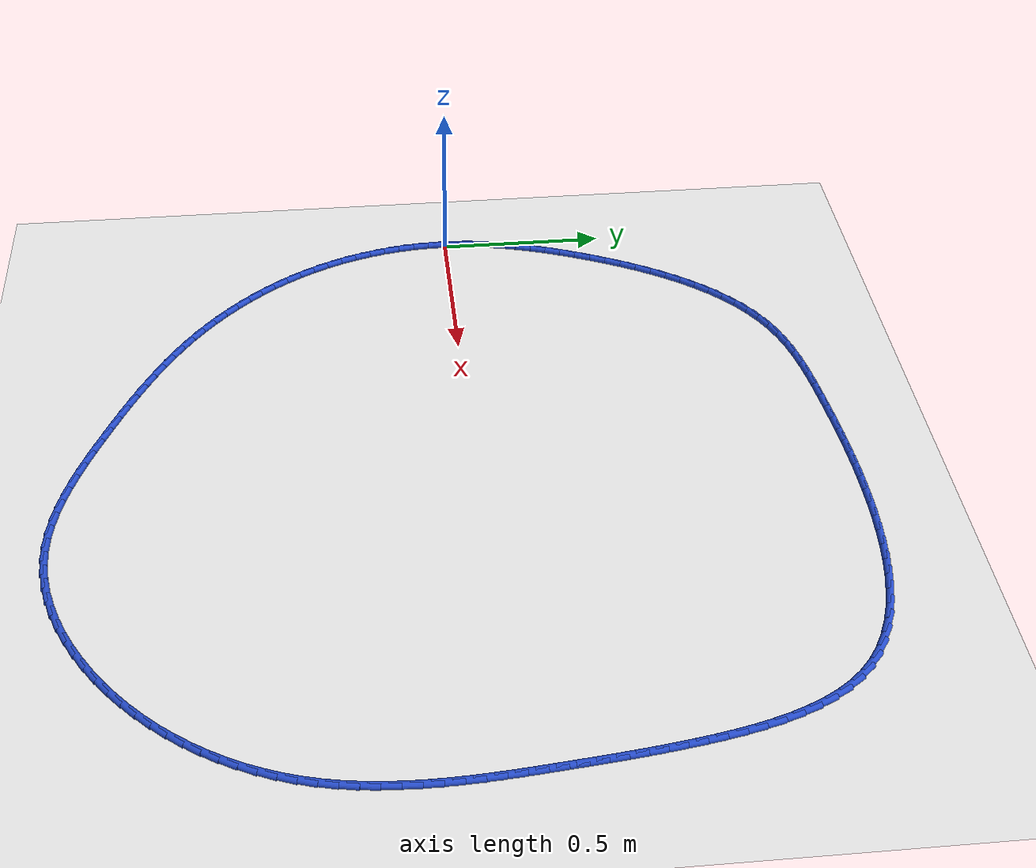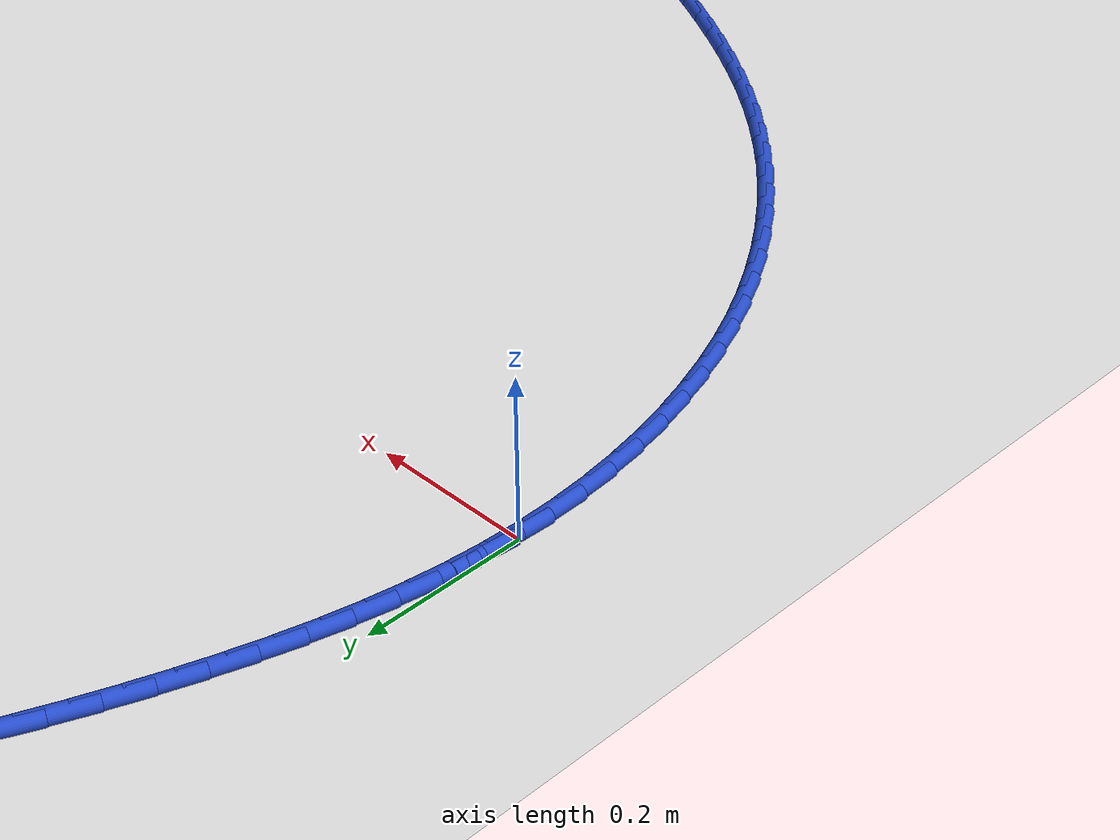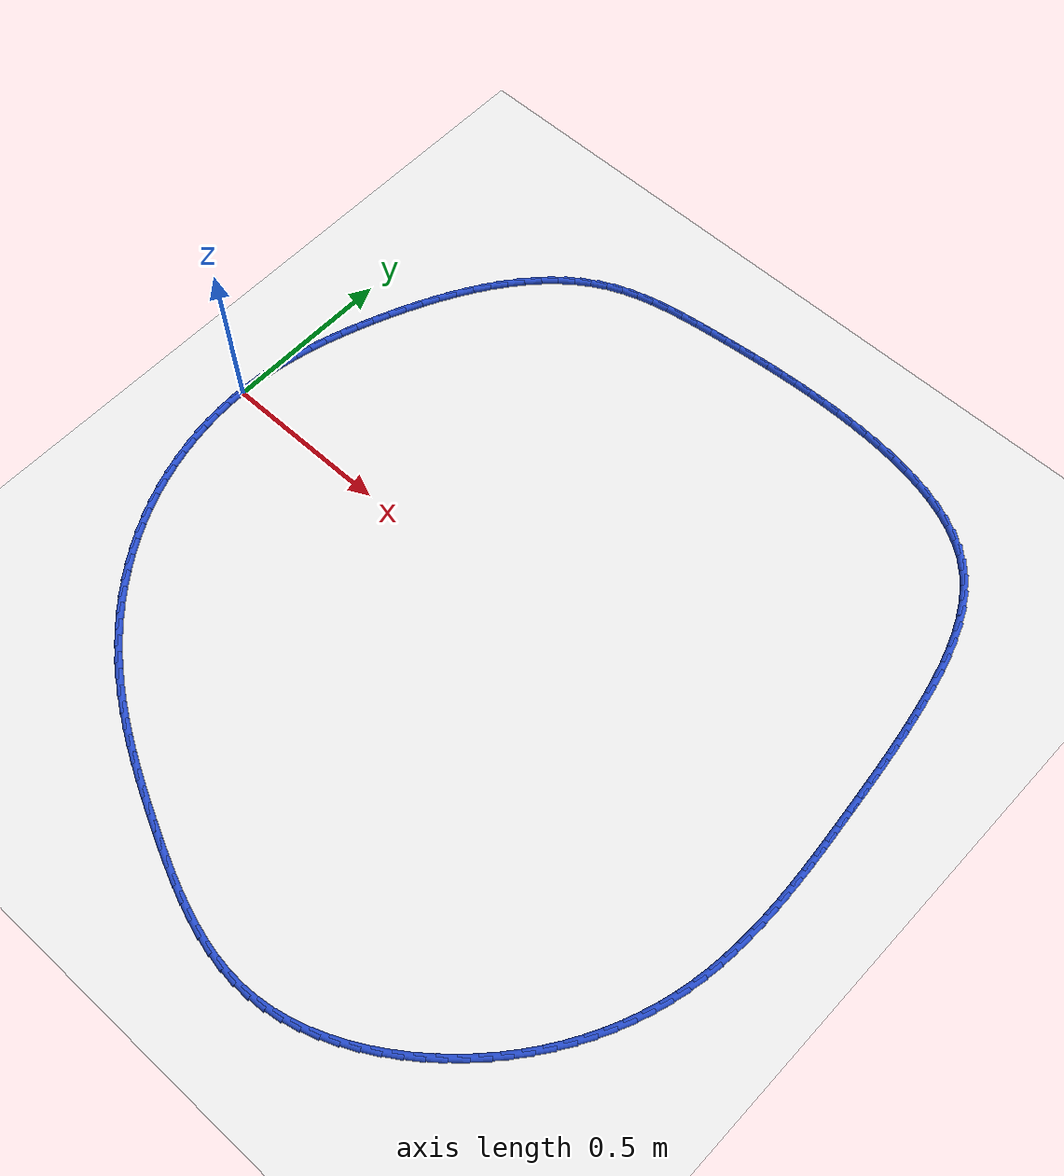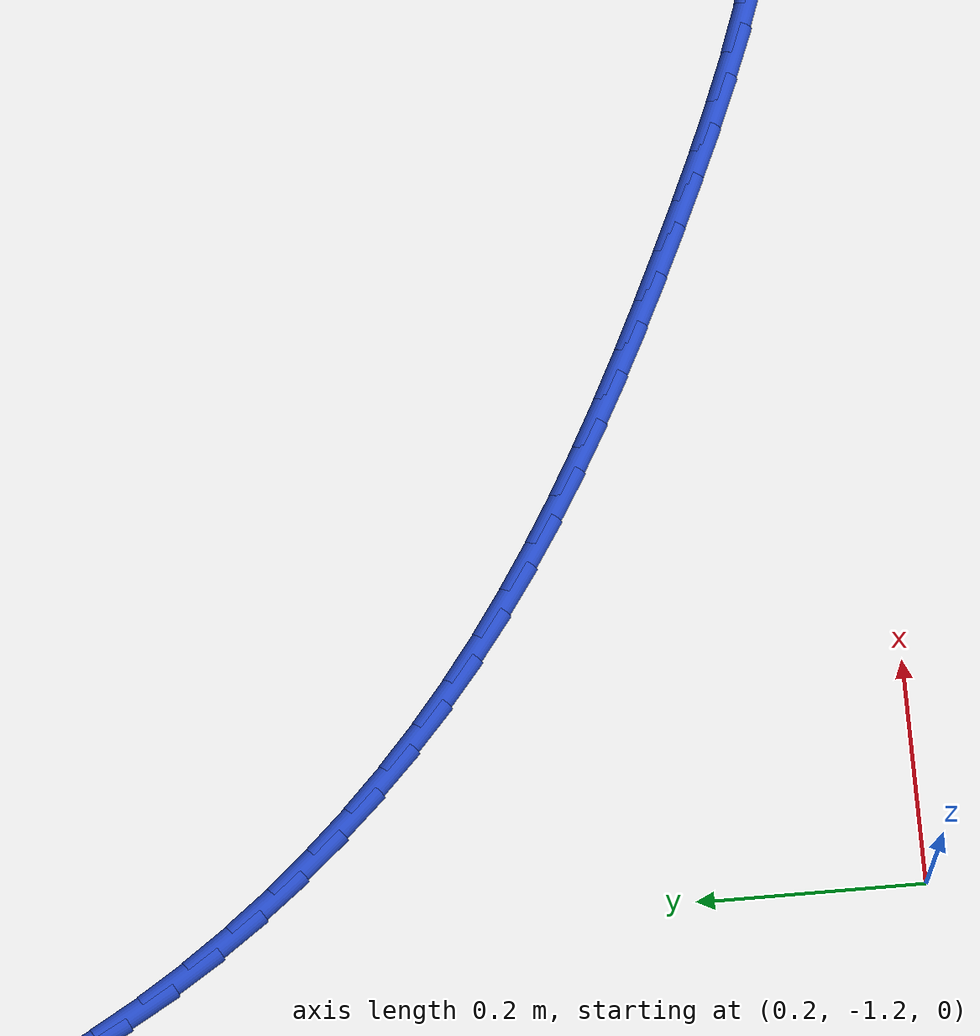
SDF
<sdf version="1.6">
 <world name="default">
  <light name="sun" type="directional">
   <pose>0 0 10 0 -0 0</pose>
   <diffuse>0.8 0.8 0.8 1</diffuse>
   <specular>0.2 0.2 0.2 1</specular>
   <attenuation>
    <range>1000</range>
    <constant>0.9</constant>
    <linear>0.01</linear>
    <quadratic>0.001</quadratic>
   </attenuation>
   <direction>-0.5 0.1 -0.9</direction>
  </light>
  <model name="ground_plane">
   <static>1</static>
   <link name="link">
    <collision name="collision">
     <geometry><plane><normal>0 0 1</normal><size>100 100</size></plane></geometry>
     <surface><friction><ode><mu>100</mu><mu2>50</mu2></ode></friction></surface>
    </collision>
    <visual name="visual">
     <cast_shadows>0</cast_shadows>
     <geometry><plane><normal>0 0 1</normal><size>100 100</size></plane></geometry>
     <material>
      <script><uri>file://media/materials/scripts/gazebo.material</uri><name>Gazebo/WhiteGlow</name></script>
     </material>
    </visual>
   </link>
  </model>
  <gravity>0 0 -9.8</gravity>
  <magnetic_field>6e-06 2.3e-05 -4.2e-05</magnetic_field>
  <atmosphere type="adiabatic"/>
  <physics name="default_physics" default="0" type="ode">
   <max_step_size>0.001</max_step_size>
   <real_time_factor>1</real_time_factor>
   <real_time_update_rate>1000</real_time_update_rate>
  </physics>
  <scene><ambient>0.4 0.4 0.4 1</ambient><background>0.7 0.7 0.7 1</background><shadows>1</shadows></scene>
  <spherical_coordinates>
   <surface_model>EARTH_WGS84</surface_model>
   <latitude_deg>0</latitude_deg>
   <longitude_deg>0</longitude_deg>
   <elevation>0</elevation>
   <heading_deg>0</heading_deg>
  </spherical_coordinates>
  <model name="line">
   <link name="link_0">
    <pose>1.734723475976807e-18 2.7755575615628914e-17 0.01 0 1.57 1.5278195043209304</pose>
    <collision name="collision">
     <geometry><cylinder><radius>0.01</radius><length>0.08</length></cylinder></geometry>
    </collision>
    <visual name="visual">
     <material>
      <script><name>Gazebo/Blue</name><uri>file://media/materials/scripts/gazebo.material</uri></script>
     </material>
     <geometry><cylinder><radius>0.01</radius><length>0.08</length></cylinder></geometry>
    </visual>
   </link>
   <link name="link_1">
    <pose>0.002061508336502274 0.047938373631018355 0.01 0 1.57 1.4752928590104364</pose>
    <collision name="collision">
     <geometry><cylinder><radius>0.01</radius><length>0.08</length></cylinder></geometry>
    </collision>
    <visual name="visual">
     <material>
      <script><name>Gazebo/Blue</name><uri>file://media/materials/scripts/gazebo.material</uri></script>
     </material>
     <geometry><cylinder><radius>0.01</radius><length>0.08</length></cylinder></geometry>
    </visual>
   </link>
   <link name="link_2">
    <pose>0.00662725512407017 0.09560006787530616 0.01 0 1.57 1.4260237001838905</pose>
    <collision name="collision">
     <geometry><cylinder><radius>0.01</radius><length>0.08</length></cylinder></geometry>
    </collision>
    <visual name="visual">
     <material>
      <script><name>Gazebo/Blue</name><uri>file://media/materials/scripts/gazebo.material</uri></script>
     </material>
     <geometry><cylinder><radius>0.01</radius><length>0.08</length></cylinder></geometry>
    </visual>
   </link>
   <link name="link_3">
    <pose>0.01354250712199076 0.1430321826391709 0.01 0 1.57 1.3803273264530966</pose>
    <collision name="collision">
     <geometry><cylinder><radius>0.01</radius><length>0.08</length></cylinder></geometry>
    </collision>
    <visual name="visual">
     <material>
      <script><name>Gazebo/Blue</name><uri>file://media/materials/scripts/gazebo.material</uri></script>
     </material>
     <geometry><cylinder><radius>0.01</radius><length>0.08</length></cylinder></geometry>
    </visual>
   </link>
   <link name="link_4">
    <pose>0.022652531089551117 0.19028181782891987 0.01 0 1.57 1.3384117648278857</pose>
    <collision name="collision">
     <geometry><cylinder><radius>0.01</radius><length>0.08</length></cylinder></geometry>
    </collision>
    <visual name="visual">
     <material>
      <script><name>Gazebo/Blue</name><uri>file://media/materials/scripts/gazebo.material</uri></script>
     </material>
     <geometry><cylinder><radius>0.01</radius><length>0.08</length></cylinder></geometry>
    </visual>
   </link>
   <link name="link_5">
    <pose>0.033802593786038344 0.23739607335086071 0.01 0 1.57 1.300390533284064</pose>
    <collision name="collision">
     <geometry><cylinder><radius>0.01</radius><length>0.08</length></cylinder></geometry>
    </collision>
    <visual name="visual">
     <material>
      <script><name>Gazebo/Blue</name><uri>file://media/materials/scripts/gazebo.material</uri></script>
     </material>
     <geometry><cylinder><radius>0.01</radius><length>0.08</length></cylinder></geometry>
    </visual>
   </link>
   <link name="link_6">
    <pose>0.04683796197073954 0.28442204911130087 0.01 0 1.57 1.2662991908527867</pose>
    <collision name="collision">
     <geometry><cylinder><radius>0.01</radius><length>0.08</length></cylinder></geometry>
    </collision>
    <visual name="visual">
     <material>
      <script><name>Gazebo/Blue</name><uri>file://media/materials/scripts/gazebo.material</uri></script>
     </material>
     <geometry><cylinder><radius>0.01</radius><length>0.08</length></cylinder></geometry>
    </visual>
   </link>
   <link name="link_7">
    <pose>0.06160390240294175 0.33140684501654777 0.01 0 1.57 1.2361129764337027</pose>
    <collision name="collision">
     <geometry><cylinder><radius>0.01</radius><length>0.08</length></cylinder></geometry>
    </collision>
    <visual name="visual">
     <material>
      <script><name>Gazebo/Blue</name><uri>file://media/materials/scripts/gazebo.material</uri></script>
     </material>
     <geometry><cylinder><radius>0.01</radius><length>0.08</length></cylinder></geometry>
    </visual>
   </link>
   <link name="link_8">
    <pose>0.07794568184193207 0.3783975609729087 0.01 0 1.57 1.2097635870300976</pose>
    <collision name="collision">
     <geometry><cylinder><radius>0.01</radius><length>0.08</length></cylinder></geometry>
    </collision>
    <visual name="visual">
     <material>
      <script><name>Gazebo/Blue</name><uri>file://media/materials/scripts/gazebo.material</uri></script>
     </material>
     <geometry><cylinder><radius>0.01</radius><length>0.08</length></cylinder></geometry>
    </visual>
   </link>
   <link name="link_9">
    <pose>0.0957085670469976 0.4254412968866915 0.01 0 1.57 1.1865406836885097</pose>
    <collision name="collision">
     <geometry><cylinder><radius>0.01</radius><length>0.08</length></cylinder></geometry>
    </collision>
    <visual name="visual">
     <material>
      <script><name>Gazebo/Blue</name><uri>file://media/materials/scripts/gazebo.material</uri></script>
     </material>
     <geometry><cylinder><radius>0.01</radius><length>0.08</length></cylinder></geometry>
    </visual>
   </link>
   <link name="link_10">
    <pose>0.1147587307369242 0.4725536873679474 0.01 0 1.57 1.1620558361260096</pose>
    <collision name="collision">
     <geometry><cylinder><radius>0.01</radius><length>0.08</length></cylinder></geometry>
    </collision>
    <visual name="visual">
     <material>
      <script><name>Gazebo/Blue</name><uri>file://media/materials/scripts/gazebo.material</uri></script>
     </material>
     <geometry><cylinder><radius>0.01</radius><length>0.08</length></cylinder></geometry>
    </visual>
   </link>
   <link name="link_11">
    <pose>0.1351069661754311 0.5195327004665647 0.01 0 1.57 1.1342719531180012</pose>
    <collision name="collision">
     <geometry><cylinder><radius>0.01</radius><length>0.08</length></cylinder></geometry>
    </collision>
    <visual name="visual">
     <material>
      <script><name>Gazebo/Blue</name><uri>file://media/materials/scripts/gazebo.material</uri></script>
     </material>
     <geometry><cylinder><radius>0.01</radius><length>0.08</length></cylinder></geometry>
    </visual>
   </link>
   <link name="link_12">
    <pose>0.15682520948886072 0.5660842788802112 0.01 0 1.57 1.1028720318219527</pose>
    <collision name="collision">
     <geometry><cylinder><radius>0.01</radius><length>0.08</length></cylinder></geometry>
    </collision>
    <visual name="visual">
     <material>
      <script><name>Gazebo/Blue</name><uri>file://media/materials/scripts/gazebo.material</uri></script>
     </material>
     <geometry><cylinder><radius>0.01</radius><length>0.08</length></cylinder></geometry>
    </visual>
   </link>
   <link name="link_13">
    <pose>0.1799856146416777 0.6119140374411416 0.01 0 1.57 1.0674861008657033</pose>
    <collision name="collision">
     <geometry><cylinder><radius>0.01</radius><length>0.08</length></cylinder></geometry>
    </collision>
    <visual name="visual">
     <material>
      <script><name>Gazebo/Blue</name><uri>file://media/materials/scripts/gazebo.material</uri></script>
     </material>
     <geometry><cylinder><radius>0.01</radius><length>0.08</length></cylinder></geometry>
    </visual>
   </link>
   <link name="link_14">
    <pose>0.20466033559834662 0.6567275909816106 0.01 0 1.57 1.027686762469743</pose>
    <collision name="collision">
     <geometry><cylinder><radius>0.01</radius><length>0.08</length></cylinder></geometry>
    </collision>
    <visual name="visual">
     <material>
      <script><name>Gazebo/Blue</name><uri>file://media/materials/scripts/gazebo.material</uri></script>
     </material>
     <geometry><cylinder><radius>0.01</radius><length>0.08</length></cylinder></geometry>
    </visual>
   </link>
   <link name="link_15">
    <pose>0.23092152632333215 0.7002305543338729 0.01 0 1.57 0.982994967646468</pose>
    <collision name="collision">
     <geometry><cylinder><radius>0.01</radius><length>0.08</length></cylinder></geometry>
    </collision>
    <visual name="visual">
     <material>
      <script><name>Gazebo/Blue</name><uri>file://media/materials/scripts/gazebo.material</uri></script>
     </material>
     <geometry><cylinder><radius>0.01</radius><length>0.08</length></cylinder></geometry>
    </visual>
   </link>
   <link name="link_16">
    <pose>0.25884134078109905 0.7421285423301837 0.01 0 1.57 0.9328928080031752</pose>
    <collision name="collision">
     <geometry><cylinder><radius>0.01</radius><length>0.08</length></cylinder></geometry>
    </collision>
    <visual name="visual">
     <material>
      <script><name>Gazebo/Blue</name><uri>file://media/materials/scripts/gazebo.material</uri></script>
     </material>
     <geometry><cylinder><radius>0.01</radius><length>0.08</length></cylinder></geometry>
    </visual>
   </link>
   <link name="link_17">
    <pose>0.2884919329361118 0.7821271698027971 0.01 0 1.57 0.8768476063972177</pose>
    <collision name="collision">
     <geometry><cylinder><radius>0.01</radius><length>0.08</length></cylinder></geometry>
    </collision>
    <visual name="visual">
     <material>
      <script><name>Gazebo/Blue</name><uri>file://media/materials/scripts/gazebo.material</uri></script>
     </material>
     <geometry><cylinder><radius>0.01</radius><length>0.08</length></cylinder></geometry>
    </visual>
   </link>
   <link name="link_18">
    <pose>0.31994545675283503 0.819932051583968 0.01 0 1.57 0.8143525726415654</pose>
    <collision name="collision">
     <geometry><cylinder><radius>0.01</radius><length>0.08</length></cylinder></geometry>
    </collision>
    <visual name="visual">
     <material>
      <script><name>Gazebo/Blue</name><uri>file://media/materials/scripts/gazebo.material</uri></script>
     </material>
     <geometry><cylinder><radius>0.01</radius><length>0.08</length></cylinder></geometry>
    </visual>
   </link>
   <link name="link_19">
    <pose>0.3532740661957334 0.855248802505951 0.01 0 1.57 0.7449893984221209</pose>
    <collision name="collision">
     <geometry><cylinder><radius>0.01</radius><length>0.08</length></cylinder></geometry>
    </collision>
    <visual name="visual">
     <material>
      <script><name>Gazebo/Blue</name><uri>file://media/materials/scripts/gazebo.material</uri></script>
     </material>
     <geometry><cylinder><radius>0.01</radius><length>0.08</length></cylinder></geometry>
    </visual>
   </link>
   <link name="link_20">
    <pose>0.38854991522927174 0.8877830374010015 0.01 0 1.57 0.6685160232272929</pose>
    <collision name="collision">
     <geometry><cylinder><radius>0.01</radius><length>0.08</length></cylinder></geometry>
    </collision>
    <visual name="visual">
     <material>
      <script><name>Gazebo/Blue</name><uri>file://media/materials/scripts/gazebo.material</uri></script>
     </material>
     <geometry><cylinder><radius>0.01</radius><length>0.08</length></cylinder></geometry>
    </visual>
   </link>
   <link name="link_21">
    <pose>0.42584515781791443 0.9172403711013737 0.01 0 1.57 0.5849765413739358</pose>
    <collision name="collision">
     <geometry><cylinder><radius>0.01</radius><length>0.08</length></cylinder></geometry>
    </collision>
    <visual name="visual">
     <material>
      <script><name>Gazebo/Blue</name><uri>file://media/materials/scripts/gazebo.material</uri></script>
     </material>
     <geometry><cylinder><radius>0.01</radius><length>0.08</length></cylinder></geometry>
    </visual>
   </link>
   <link name="link_22">
    <pose>0.4652319479261262 0.943326418439322 0.01 0 1.57 0.4948184956689808</pose>
    <collision name="collision">
     <geometry><cylinder><radius>0.01</radius><length>0.08</length></cylinder></geometry>
    </collision>
    <visual name="visual">
     <material>
      <script><name>Gazebo/Blue</name><uri>file://media/materials/scripts/gazebo.material</uri></script>
     </material>
     <geometry><cylinder><radius>0.01</radius><length>0.08</length></cylinder></geometry>
    </visual>
   </link>
   <link name="link_23">
    <pose>0.5067824395183717 0.9657467942471014 0.01 0 1.57 0.402084227582565</pose>
    <collision name="collision">
     <geometry><cylinder><radius>0.01</radius><length>0.08</length></cylinder></geometry>
    </collision>
    <visual name="visual">
     <material>
      <script><name>Gazebo/Blue</name><uri>file://media/materials/scripts/gazebo.material</uri></script>
     </material>
     <geometry><cylinder><radius>0.01</radius><length>0.08</length></cylinder></geometry>
    </visual>
   </link>
   <link name="link_24">
    <pose>0.5504942899350385 0.9843353539701478 0.01 0 1.57 0.3206302841895804</pose>
    <collision name="collision">
     <geometry><cylinder><radius>0.01</radius><length>0.08</length></cylinder></geometry>
    </collision>
    <visual name="visual">
     <material>
      <script><name>Gazebo/Blue</name><uri>file://media/materials/scripts/gazebo.material</uri></script>
     </material>
     <geometry><cylinder><radius>0.01</radius><length>0.08</length></cylinder></geometry>
    </visual>
   </link>
   <link name="link_25">
    <pose>0.5960522234504847 0.9994646449579873 0.01 0 1.57 0.25361632333466483</pose>
    <collision name="collision">
     <geometry><cylinder><radius>0.01</radius><length>0.08</length></cylinder></geometry>
    </collision>
    <visual name="visual">
     <material>
      <script><name>Gazebo/Blue</name><uri>file://media/materials/scripts/gazebo.material</uri></script>
     </material>
     <geometry><cylinder><radius>0.01</radius><length>0.08</length></cylinder></geometry>
    </visual>
   </link>
   <link name="link_26">
    <pose>0.6430588088947914 1.0116486392848314 0.01 0 1.57 0.20021726474361068</pose>
    <collision name="collision">
     <geometry><cylinder><radius>0.01</radius><length>0.08</length></cylinder></geometry>
    </collision>
    <visual name="visual">
     <material>
      <script><name>Gazebo/Blue</name><uri>file://media/materials/scripts/gazebo.material</uri></script>
     </material>
     <geometry><cylinder><radius>0.01</radius><length>0.08</length></cylinder></geometry>
    </visual>
   </link>
   <link name="link_27">
    <pose>0.6911166147583987 1.0214013096095613 0.01 0 1.57 0.15948511516861477</pose>
    <collision name="collision">
     <geometry><cylinder><radius>0.01</radius><length>0.08</length></cylinder></geometry>
    </collision>
    <visual name="visual">
     <material>
      <script><name>Gazebo/Blue</name><uri>file://media/materials/scripts/gazebo.material</uri></script>
     </material>
     <geometry><cylinder><radius>0.01</radius><length>0.08</length></cylinder></geometry>
    </visual>
   </link>
   <link name="link_28">
    <pose>0.7398282095317469 1.029236628591058 0.01 0 1.57 0.13060233392473475</pose>
    <collision name="collision">
     <geometry><cylinder><radius>0.01</radius><length>0.08</length></cylinder></geometry>
    </collision>
    <visual name="visual">
     <material>
      <script><name>Gazebo/Blue</name><uri>file://media/materials/scripts/gazebo.material</uri></script>
     </material>
     <geometry><cylinder><radius>0.01</radius><length>0.08</length></cylinder></geometry>
    </visual>
   </link>
   <link name="link_29">
    <pose>0.7887961617052762 1.0356685688882021 0.01 0 1.57 0.11303017697079211</pose>
    <collision name="collision">
     <geometry><cylinder><radius>0.01</radius><length>0.08</length></cylinder></geometry>
    </collision>
    <visual name="visual">
     <material>
      <script><name>Gazebo/Blue</name><uri>file://media/materials/scripts/gazebo.material</uri></script>
     </material>
     <geometry><cylinder><radius>0.01</radius><length>0.08</length></cylinder></geometry>
    </visual>
   </link>
   <link name="link_30">
    <pose>0.8376230397694265 1.0412111031598748 0.01 0 1.57 0.10499841717770726</pose>
    <collision name="collision">
     <geometry><cylinder><radius>0.01</radius><length>0.08</length></cylinder></geometry>
    </collision>
    <visual name="visual">
     <material>
      <script><name>Gazebo/Blue</name><uri>file://media/materials/scripts/gazebo.material</uri></script>
     </material>
     <geometry><cylinder><radius>0.01</radius><length>0.08</length></cylinder></geometry>
    </visual>
   </link>
   <link name="link_31">
    <pose>0.8859809220531941 1.0463073461653623 0.01 0 1.57 0.09760615085269297</pose>
    <collision name="collision">
     <geometry><cylinder><radius>0.01</radius><length>0.08</length></cylinder></geometry>
    </collision>
    <visual name="visual">
     <material>
      <script><name>Gazebo/Blue</name><uri>file://media/materials/scripts/gazebo.material</uri></script>
     </material>
     <geometry><cylinder><radius>0.01</radius><length>0.08</length></cylinder></geometry>
    </visual>
   </link>
   <link name="link_32">
    <pose>0.9339321320311835 1.0510025991757024 0.01 0 1.57 0.08776248850794602</pose>
    <collision name="collision">
     <geometry><cylinder><radius>0.01</radius><length>0.08</length></cylinder></geometry>
    </collision>
    <visual name="visual">
     <material>
      <script><name>Gazebo/Blue</name><uri>file://media/materials/scripts/gazebo.material</uri></script>
     </material>
     <geometry><cylinder><radius>0.01</radius><length>0.08</length></cylinder></geometry>
    </visual>
   </link>
   <link name="link_33">
    <pose>0.9816750867436391 1.0552034305226854 0.01 0 1.57 0.07554397021373996</pose>
    <collision name="collision">
     <geometry><cylinder><radius>0.01</radius><length>0.08</length></cylinder></geometry>
    </collision>
    <visual name="visual">
     <material>
      <script><name>Gazebo/Blue</name><uri>file://media/materials/scripts/gazebo.material</uri></script>
     </material>
     <geometry><cylinder><radius>0.01</radius><length>0.08</length></cylinder></geometry>
    </visual>
   </link>
   <link name="link_34">
    <pose>1.0294083434975336 1.0588162655510671 0.01 0 1.57 0.061091136379166314</pose>
    <collision name="collision">
     <geometry><cylinder><radius>0.01</radius><length>0.08</length></cylinder></geometry>
    </collision>
    <visual name="visual">
     <material>
      <script><name>Gazebo/Blue</name><uri>file://media/materials/scripts/gazebo.material</uri></script>
     </material>
     <geometry><cylinder><radius>0.01</radius><length>0.08</length></cylinder></geometry>
    </visual>
   </link>
   <link name="link_35">
    <pose>1.077330459599841 1.0617475296056025 0.01 0 1.57 0.0446017251811088</pose>
    <collision name="collision">
     <geometry><cylinder><radius>0.01</radius><length>0.08</length></cylinder></geometry>
    </collision>
    <visual name="visual">
     <material>
      <script><name>Gazebo/Blue</name><uri>file://media/materials/scripts/gazebo.material</uri></script>
     </material>
     <geometry><cylinder><radius>0.01</radius><length>0.08</length></cylinder></geometry>
    </visual>
   </link>
   <link name="link_36">
    <pose>1.1256399923575338 1.0639036480310473 0.01 0 1.57 0.026323497929840085</pose>
    <collision name="collision">
     <geometry><cylinder><radius>0.01</radius><length>0.08</length></cylinder></geometry>
    </collision>
    <visual name="visual">
     <material>
      <script><name>Gazebo/Blue</name><uri>file://media/materials/scripts/gazebo.material</uri></script>
     </material>
     <geometry><cylinder><radius>0.01</radius><length>0.08</length></cylinder></geometry>
    </visual>
   </link>
   <link name="link_37">
    <pose>1.1745354990775845 1.0651910461721563 0.01 0 1.57 0.006543846868040155</pose>
    <collision name="collision">
     <geometry><cylinder><radius>0.01</radius><length>0.08</length></cylinder></geometry>
    </collision>
    <visual name="visual">
     <material>
      <script><name>Gazebo/Blue</name><uri>file://media/materials/scripts/gazebo.material</uri></script>
     </material>
     <geometry><cylinder><radius>0.01</radius><length>0.08</length></cylinder></geometry>
    </visual>
   </link>
   <link name="link_38">
    <pose>1.2242155370669672 1.0655161493736862 0.01 0 1.57 -0.014594561211399498</pose>
    <collision name="collision">
     <geometry><cylinder><radius>0.01</radius><length>0.08</length></cylinder></geometry>
    </collision>
    <visual name="visual">
     <material>
      <script><name>Gazebo/Blue</name><uri>file://media/materials/scripts/gazebo.material</uri></script>
     </material>
     <geometry><cylinder><radius>0.01</radius><length>0.08</length></cylinder></geometry>
    </visual>
   </link>
   <link name="link_39">
    <pose>1.2748469841931045 1.0647771531496053 0.01 0 1.57 -0.03883700470863113</pose>
    <collision name="collision">
     <geometry><cylinder><radius>0.01</radius><length>0.08</length></cylinder></geometry>
    </collision>
    <visual name="visual">
     <material>
      <script><name>Gazebo/Blue</name><uri>file://media/materials/scripts/gazebo.material</uri></script>
     </material>
     <geometry><cylinder><radius>0.01</radius><length>0.08</length></cylinder></geometry>
    </visual>
   </link>
   <link name="link_40">
    <pose>1.3262420598524998 1.0627801182020307 0.01 0 1.57 -0.06766321029863363</pose>
    <collision name="collision">
     <geometry><cylinder><radius>0.01</radius><length>0.08</length></cylinder></geometry>
    </collision>
    <visual name="visual">
     <material>
      <script><name>Gazebo/Blue</name><uri>file://media/materials/scripts/gazebo.material</uri></script>
     </material>
     <geometry><cylinder><radius>0.01</radius><length>0.08</length></cylinder></geometry>
    </visual>
   </link>
   <link name="link_41">
    <pose>1.3779904748190344 1.0592733009177675 0.01 0 1.57 -0.10159209715488299</pose>
    <collision name="collision">
     <geometry><cylinder><radius>0.01</radius><length>0.08</length></cylinder></geometry>
    </collision>
    <visual name="visual">
     <material>
      <script><name>Gazebo/Blue</name><uri>file://media/materials/scripts/gazebo.material</uri></script>
     </material>
     <geometry><cylinder><radius>0.01</radius><length>0.08</length></cylinder></geometry>
    </visual>
   </link>
   <link name="link_42">
    <pose>1.4296785045673628 1.0540040652457585 0.01 0 1.57 -0.14128497044938518</pose>
    <collision name="collision">
     <geometry><cylinder><radius>0.01</radius><length>0.08</length></cylinder></geometry>
    </collision>
    <visual name="visual">
     <material>
      <script><name>Gazebo/Blue</name><uri>file://media/materials/scripts/gazebo.material</uri></script>
     </material>
     <geometry><cylinder><radius>0.01</radius><length>0.08</length></cylinder></geometry>
    </visual>
   </link>
   <link name="link_43">
    <pose>1.4808924245721409 1.0467197751349457 0.01 0 1.57 -0.1875706249761669</pose>
    <collision name="collision">
     <geometry><cylinder><radius>0.01</radius><length>0.08</length></cylinder></geometry>
    </collision>
    <visual name="visual">
     <material>
      <script><name>Gazebo/Blue</name><uri>file://media/materials/scripts/gazebo.material</uri></script>
     </material>
     <geometry><cylinder><radius>0.01</radius><length>0.08</length></cylinder></geometry>
    </visual>
   </link>
   <link name="link_44">
    <pose>1.5312185103080245 1.0371677945342719 0.01 0 1.57 -0.24144648340928193</pose>
    <collision name="collision">
     <geometry><cylinder><radius>0.01</radius><length>0.08</length></cylinder></geometry>
    </collision>
    <visual name="visual">
     <material>
      <script><name>Gazebo/Blue</name><uri>file://media/materials/scripts/gazebo.material</uri></script>
     </material>
     <geometry><cylinder><radius>0.01</radius><length>0.08</length></cylinder></geometry>
    </visual>
   </link>
   <link name="link_45">
    <pose>1.580243037249668 1.0250954873926796 0.01 0 1.57 -0.30406163387184343</pose>
    <collision name="collision">
     <geometry><cylinder><radius>0.01</radius><length>0.08</length></cylinder></geometry>
    </collision>
    <visual name="visual">
     <material>
      <script><name>Gazebo/Blue</name><uri>file://media/materials/scripts/gazebo.material</uri></script>
     </material>
     <geometry><cylinder><radius>0.01</radius><length>0.08</length></cylinder></geometry>
    </visual>
   </link>
   <link name="link_46">
    <pose>1.627552280871728 1.0102502176591113 0.01 0 1.57 -0.37666096547751804</pose>
    <collision name="collision">
     <geometry><cylinder><radius>0.01</radius><length>0.08</length></cylinder></geometry>
    </collision>
    <visual name="visual">
     <material>
      <script><name>Gazebo/Blue</name><uri>file://media/materials/scripts/gazebo.material</uri></script>
     </material>
     <geometry><cylinder><radius>0.01</radius><length>0.08</length></cylinder></geometry>
    </visual>
   </link>
   <link name="link_47">
    <pose>1.6727325166488594 0.9923793492825097 0.01 0 1.57 -0.4604594581554081</pose>
    <collision name="collision">
     <geometry><cylinder><radius>0.01</radius><length>0.08</length></cylinder></geometry>
    </collision>
    <visual name="visual">
     <material>
      <script><name>Gazebo/Blue</name><uri>file://media/materials/scripts/gazebo.material</uri></script>
     </material>
     <geometry><cylinder><radius>0.01</radius><length>0.08</length></cylinder></geometry>
    </visual>
   </link>
   <link name="link_48">
    <pose>1.7153700200557183 0.9712302462118169 0.01 0 1.57 -0.5564093542732482</pose>
    <collision name="collision">
     <geometry><cylinder><radius>0.01</radius><length>0.08</length></cylinder></geometry>
    </collision>
    <visual name="visual">
     <material>
      <script><name>Gazebo/Blue</name><uri>file://media/materials/scripts/gazebo.material</uri></script>
     </material>
     <geometry><cylinder><radius>0.01</radius><length>0.08</length></cylinder></geometry>
    </visual>
   </link>
   <link name="link_49">
    <pose>1.7550510665669588 0.9465502723959759 0.01 0 1.57 -0.6648361354555788</pose>
    <collision name="collision">
     <geometry><cylinder><radius>0.01</radius><length>0.08</length></cylinder></geometry>
    </collision>
    <visual name="visual">
     <material>
      <script><name>Gazebo/Blue</name><uri>file://media/materials/scripts/gazebo.material</uri></script>
     </material>
     <geometry><cylinder><radius>0.01</radius><length>0.08</length></cylinder></geometry>
    </visual>
   </link>
   <link name="link_50">
    <pose>1.7913619316572378 0.9180867917839286 0.01 0 1.57 -0.7845811259198384</pose>
    <collision name="collision">
     <geometry><cylinder><radius>0.01</radius><length>0.08</length></cylinder></geometry>
    </collision>
    <visual name="visual">
     <material>
      <script><name>Gazebo/Blue</name><uri>file://media/materials/scripts/gazebo.material</uri></script>
     </material>
     <geometry><cylinder><radius>0.01</radius><length>0.08</length></cylinder></geometry>
    </visual>
   </link>
   <link name="link_51">
    <pose>1.823901554734521 0.8856002974933804 0.01 0 1.57 -0.9031709341815312</pose>
    <collision name="collision">
     <geometry><cylinder><radius>0.01</radius><length>0.08</length></cylinder></geometry>
    </collision>
    <visual name="visual">
     <material>
      <script><name>Gazebo/Blue</name><uri>file://media/materials/scripts/gazebo.material</uri></script>
     </material>
     <geometry><cylinder><radius>0.01</radius><length>0.08</length></cylinder></geometry>
    </visual>
   </link>
   <link name="link_52">
    <pose>1.8526020337529767 0.8491966804477683 0.01 0 1.57 -1.0077063952306282</pose>
    <collision name="collision">
     <geometry><cylinder><radius>0.01</radius><length>0.08</length></cylinder></geometry>
    </collision>
    <visual name="visual">
     <material>
      <script><name>Gazebo/Blue</name><uri>file://media/materials/scripts/gazebo.material</uri></script>
     </material>
     <geometry><cylinder><radius>0.01</radius><length>0.08</length></cylinder></geometry>
    </visual>
   </link>
   <link name="link_53">
    <pose>1.8777537049039736 0.8093532304209262 0.01 0 1.57 -1.097528058521291</pose>
    <collision name="collision">
     <geometry><cylinder><radius>0.01</radius><length>0.08</length></cylinder></geometry>
    </collision>
    <visual name="visual">
     <material>
      <script><name>Gazebo/Blue</name><uri>file://media/materials/scripts/gazebo.material</uri></script>
     </material>
     <geometry><cylinder><radius>0.01</radius><length>0.08</length></cylinder></geometry>
    </visual>
   </link>
   <link name="link_54">
    <pose>1.8996645925349527 0.766565575153295 0.01 0 1.57 -1.1735646982423504</pose>
    <collision name="collision">
     <geometry><cylinder><radius>0.01</radius><length>0.08</length></cylinder></geometry>
    </collision>
    <visual name="visual">
     <material>
      <script><name>Gazebo/Blue</name><uri>file://media/materials/scripts/gazebo.material</uri></script>
     </material>
     <geometry><cylinder><radius>0.01</radius><length>0.08</length></cylinder></geometry>
    </visual>
   </link>
   <link name="link_55">
    <pose>1.9186427209933583 0.7213293423853167 0.01 0 1.57 -1.2371986365955125</pose>
    <collision name="collision">
     <geometry><cylinder><radius>0.01</radius><length>0.08</length></cylinder></geometry>
    </collision>
    <visual name="visual">
     <material>
      <script><name>Gazebo/Blue</name><uri>file://media/materials/scripts/gazebo.material</uri></script>
     </material>
     <geometry><cylinder><radius>0.01</radius><length>0.08</length></cylinder></geometry>
    </visual>
   </link>
   <link name="link_56">
    <pose>1.9349961146266323 0.6741401598574334 0.01 0 1.57 -1.2898819806516661</pose>
    <collision name="collision">
     <geometry><cylinder><radius>0.01</radius><length>0.08</length></cylinder></geometry>
    </collision>
    <visual name="visual">
     <material>
      <script><name>Gazebo/Blue</name><uri>file://media/materials/scripts/gazebo.material</uri></script>
     </material>
     <geometry><cylinder><radius>0.01</radius><length>0.08</length></cylinder></geometry>
    </visual>
   </link>
   <link name="link_57">
    <pose>1.949032797782218 0.6254936553100867 0.01 0 1.57 -1.332926757492975</pose>
    <collision name="collision">
     <geometry><cylinder><radius>0.01</radius><length>0.08</length></cylinder></geometry>
    </collision>
    <visual name="visual">
     <material>
      <script><name>Gazebo/Blue</name><uri>file://media/materials/scripts/gazebo.material</uri></script>
     </material>
     <geometry><cylinder><radius>0.01</radius><length>0.08</length></cylinder></geometry>
    </visual>
   </link>
   <link name="link_58">
    <pose>1.9610607948075578 0.575885456483719 0.01 0 1.57 -1.3674076708182594</pose>
    <collision name="collision">
     <geometry><cylinder><radius>0.01</radius><length>0.08</length></cylinder></geometry>
    </collision>
    <visual name="visual">
     <material>
      <script><name>Gazebo/Blue</name><uri>file://media/materials/scripts/gazebo.material</uri></script>
     </material>
     <geometry><cylinder><radius>0.01</radius><length>0.08</length></cylinder></geometry>
    </visual>
   </link>
   <link name="link_59">
    <pose>1.971388130050095 0.5258111911187717 0.01 0 1.57 -1.3941234215570681</pose>
    <collision name="collision">
     <geometry><cylinder><radius>0.01</radius><length>0.08</length></cylinder></geometry>
    </collision>
    <visual name="visual">
     <material>
      <script><name>Gazebo/Blue</name><uri>file://media/materials/scripts/gazebo.material</uri></script>
     </material>
     <geometry><cylinder><radius>0.01</radius><length>0.08</length></cylinder></geometry>
    </visual>
   </link>
   <link name="link_60">
    <pose>1.9803228278572718 0.47576648695568724 0.01 0 1.57 -1.4136600682739369</pose>
    <collision name="collision">
     <geometry><cylinder><radius>0.01</radius><length>0.08</length></cylinder></geometry>
    </collision>
    <visual name="visual">
     <material>
      <script><name>Gazebo/Blue</name><uri>file://media/materials/scripts/gazebo.material</uri></script>
     </material>
     <geometry><cylinder><radius>0.01</radius><length>0.08</length></cylinder></geometry>
    </visual>
   </link>
   <link name="link_61">
    <pose>1.9881703773529116 0.42623716161352854 0.01 0 1.57 -1.4286281256002147</pose>
    <collision name="collision">
     <geometry><cylinder><radius>0.01</radius><length>0.08</length></cylinder></geometry>
    </collision>
    <visual name="visual">
     <material>
      <script><name>Gazebo/Blue</name><uri>file://media/materials/scripts/gazebo.material</uri></script>
     </material>
     <geometry><cylinder><radius>0.01</radius><length>0.08</length></cylinder></geometry>
    </visual>
   </link>
   <link name="link_62">
    <pose>1.9951591222733742 0.3774105163956057 0.01 0 1.57 -1.4416793062806386</pose>
    <collision name="collision">
     <geometry><cylinder><radius>0.01</radius><length>0.08</length></cylinder></geometry>
    </collision>
    <visual name="visual">
     <material>
      <script><name>Gazebo/Blue</name><uri>file://media/materials/scripts/gazebo.material</uri></script>
     </material>
     <geometry><cylinder><radius>0.01</radius><length>0.08</length></cylinder></geometry>
    </visual>
   </link>
   <link name="link_63">
    <pose>2.001428071097467 0.32912816723336275 0.01 0 1.57 -1.4527402589697305</pose>
    <collision name="collision">
     <geometry><cylinder><radius>0.01</radius><length>0.08</length></cylinder></geometry>
    </collision>
    <visual name="visual">
     <material>
      <script><name>Gazebo/Blue</name><uri>file://media/materials/scripts/gazebo.material</uri></script>
     </material>
     <geometry><cylinder><radius>0.01</radius><length>0.08</length></cylinder></geometry>
    </visual>
   </link>
   <link name="link_64">
    <pose>2.0071112426461846 0.2812124224325322 0.01 0 1.57 -1.4616206004657732</pose>
    <collision name="collision">
     <geometry><cylinder><radius>0.01</radius><length>0.08</length></cylinder></geometry>
    </collision>
    <visual name="visual">
     <material>
      <script><name>Gazebo/Blue</name><uri>file://media/materials/scripts/gazebo.material</uri></script>
     </material>
     <geometry><cylinder><radius>0.01</radius><length>0.08</length></cylinder></geometry>
    </visual>
   </link>
   <link name="link_65">
    <pose>2.012342655740523 0.2334855902988454 0.01 0 1.57 -1.4681797207583678</pose>
    <collision name="collision">
     <geometry><cylinder><radius>0.01</radius><length>0.08</length></cylinder></geometry>
    </collision>
    <visual name="visual">
     <material>
      <script><name>Gazebo/Blue</name><uri>file://media/materials/scripts/gazebo.material</uri></script>
     </material>
     <geometry><cylinder><radius>0.01</radius><length>0.08</length></cylinder></geometry>
    </visual>
   </link>
   <link name="link_66">
    <pose>2.017256329201478 0.18576997913803384 0.01 0 1.57 -1.4723324187671432</pose>
    <collision name="collision">
     <geometry><cylinder><radius>0.01</radius><length>0.08</length></cylinder></geometry>
    </collision>
    <visual name="visual">
     <material>
      <script><name>Gazebo/Blue</name><uri>file://media/materials/scripts/gazebo.material</uri></script>
     </material>
     <geometry><cylinder><radius>0.01</radius><length>0.08</length></cylinder></geometry>
    </visual>
   </link>
   <link name="link_67">
    <pose>2.0219862818500434 0.1378878972558299 0.01 0 1.57 -1.4745955139588494</pose>
    <collision name="collision">
     <geometry><cylinder><radius>0.01</radius><length>0.08</length></cylinder></geometry>
    </collision>
    <visual name="visual">
     <material>
      <script><name>Gazebo/Blue</name><uri>file://media/materials/scripts/gazebo.material</uri></script>
     </material>
     <geometry><cylinder><radius>0.01</radius><length>0.08</length></cylinder></geometry>
    </visual>
   </link>
   <link name="link_68">
    <pose>2.026637991394799 0.08968299494147082 0.01 0 1.57 -1.4790407924561708</pose>
    <collision name="collision">
     <geometry><cylinder><radius>0.01</radius><length>0.08</length></cylinder></geometry>
    </collision>
    <visual name="visual">
     <material>
      <script><name>Gazebo/Blue</name><uri>file://media/materials/scripts/gazebo.material</uri></script>
     </material>
     <geometry><cylinder><radius>0.01</radius><length>0.08</length></cylinder></geometry>
    </visual>
   </link>
   <link name="link_69">
    <pose>2.031102874562708 0.041158989333452 0.01 0 1.57 -1.487484022941152</pose>
    <collision name="collision">
     <geometry><cylinder><radius>0.01</radius><length>0.08</length></cylinder></geometry>
    </collision>
    <visual name="visual">
     <material>
      <script><name>Gazebo/Blue</name><uri>file://media/materials/scripts/gazebo.material</uri></script>
     </material>
     <geometry><cylinder><radius>0.01</radius><length>0.08</length></cylinder></geometry>
    </visual>
   </link>
   <link name="link_70">
    <pose>2.035175168973286 -0.007607735503580903 0.01 0 1.57 -1.4999308004067775</pose>
    <collision name="collision">
     <geometry><cylinder><radius>0.01</radius><length>0.08</length></cylinder></geometry>
    </collision>
    <visual name="visual">
     <material>
      <script><name>Gazebo/Blue</name><uri>file://media/materials/scripts/gazebo.material</uri></script>
     </material>
     <geometry><cylinder><radius>0.01</radius><length>0.08</length></cylinder></geometry>
    </visual>
   </link>
   <link name="link_71">
    <pose>2.0386486267266166 -0.056540432451587415 0.01 0 1.57 -1.5164177463807949</pose>
    <collision name="collision">
     <geometry><cylinder><radius>0.01</radius><length>0.08</length></cylinder></geometry>
    </collision>
    <visual name="visual">
     <material>
      <script><name>Gazebo/Blue</name><uri>file://media/materials/scripts/gazebo.material</uri></script>
     </material>
     <geometry><cylinder><radius>0.01</radius><length>0.08</length></cylinder></geometry>
    </visual>
   </link>
   <link name="link_72">
    <pose>2.0413169999227825 -0.10556235439252819 0.01 0 1.57 -1.537015748280475</pose>
    <collision name="collision">
     <geometry><cylinder><radius>0.01</radius><length>0.08</length></cylinder></geometry>
    </collision>
    <visual name="visual">
     <material>
      <script><name>Gazebo/Blue</name><uri>file://media/materials/scripts/gazebo.material</uri></script>
     </material>
     <geometry><cylinder><radius>0.01</radius><length>0.08</length></cylinder></geometry>
    </visual>
   </link>
   <link name="link_73">
    <pose>2.0429740406618677 -0.15459675420836422 0.01 0 1.57 -1.561822518058569</pose>
    <collision name="collision">
     <geometry><cylinder><radius>0.01</radius><length>0.08</length></cylinder></geometry>
    </collision>
    <visual name="visual">
     <material>
      <script><name>Gazebo/Blue</name><uri>file://media/materials/scripts/gazebo.material</uri></script>
     </material>
     <geometry><cylinder><radius>0.01</radius><length>0.08</length></cylinder></geometry>
    </visual>
   </link>
   <link name="link_74">
    <pose>2.043413501043954 -0.20356688478105434 0.01 0 1.57 1.5506396114186878</pose>
    <collision name="collision">
     <geometry><cylinder><radius>0.01</radius><length>0.08</length></cylinder></geometry>
    </collision>
    <visual name="visual">
     <material>
      <script><name>Gazebo/Blue</name><uri>file://media/materials/scripts/gazebo.material</uri></script>
     </material>
     <geometry><cylinder><radius>0.01</radius><length>0.08</length></cylinder></geometry>
    </visual>
   </link>
   <link name="link_75">
    <pose>2.042429133169126 -0.2523959989925595 0.01 0 1.57 1.5170655100059542</pose>
    <collision name="collision">
     <geometry><cylinder><radius>0.01</radius><length>0.08</length></cylinder></geometry>
    </collision>
    <visual name="visual">
     <material>
      <script><name>Gazebo/Blue</name><uri>file://media/materials/scripts/gazebo.material</uri></script>
     </material>
     <geometry><cylinder><radius>0.01</radius><length>0.08</length></cylinder></geometry>
    </visual>
   </link>
   <link name="link_76">
    <pose>2.0398146891374678 -0.3010073497248401 0.01 0 1.57 1.4789392658281038</pose>
    <collision name="collision">
     <geometry><cylinder><radius>0.01</radius><length>0.08</length></cylinder></geometry>
    </collision>
    <visual name="visual">
     <material>
      <script><name>Gazebo/Blue</name><uri>file://media/materials/scripts/gazebo.material</uri></script>
     </material>
     <geometry><cylinder><radius>0.01</radius><length>0.08</length></cylinder></geometry>
    </visual>
   </link>
   <link name="link_77">
    <pose>2.0353639210490604 -0.34932418985985625 0.01 0 1.57 1.4361838894595038</pose>
    <collision name="collision">
     <geometry><cylinder><radius>0.01</radius><length>0.08</length></cylinder></geometry>
    </collision>
    <visual name="visual">
     <material>
      <script><name>Gazebo/Blue</name><uri>file://media/materials/scripts/gazebo.material</uri></script>
     </material>
     <geometry><cylinder><radius>0.01</radius><length>0.08</length></cylinder></geometry>
    </visual>
   </link>
   <link name="link_78">
    <pose>2.028870581003989 -0.3972697722795691 0.01 0 1.57 1.3887785797312417</pose>
    <collision name="collision">
     <geometry><cylinder><radius>0.01</radius><length>0.08</length></cylinder></geometry>
    </collision>
    <visual name="visual">
     <material>
      <script><name>Gazebo/Blue</name><uri>file://media/materials/scripts/gazebo.material</uri></script>
     </material>
     <geometry><cylinder><radius>0.01</radius><length>0.08</length></cylinder></geometry>
    </visual>
   </link>
   <link name="link_79">
    <pose>2.020128421102335 -0.4447673498659374 0.01 0 1.57 1.336805619706383</pose>
    <collision name="collision">
     <geometry><cylinder><radius>0.01</radius><length>0.08</length></cylinder></geometry>
    </collision>
    <visual name="visual">
     <material>
      <script><name>Gazebo/Blue</name><uri>file://media/materials/scripts/gazebo.material</uri></script>
     </material>
     <geometry><cylinder><radius>0.01</radius><length>0.08</length></cylinder></geometry>
    </visual>
   </link>
   <link name="link_80">
    <pose>2.008932147821717 -0.4917400929331125 0.01 0 1.57 1.2821634019810964</pose>
    <collision name="collision">
     <geometry><cylinder><radius>0.01</radius><length>0.08</length></cylinder></geometry>
    </collision>
    <visual name="visual">
     <material>
      <script><name>Gazebo/Blue</name><uri>file://media/materials/scripts/gazebo.material</uri></script>
     </material>
     <geometry><cylinder><radius>0.01</radius><length>0.08</length></cylinder></geometry>
    </visual>
   </link>
   <link name="link_81">
    <pose>1.9951657276863322 -0.5381034494775226 0.01 0 1.57 1.2280390384629372</pose>
    <collision name="collision">
     <geometry><cylinder><radius>0.01</radius><length>0.08</length></cylinder></geometry>
    </collision>
    <visual name="visual">
     <material>
      <script><name>Gazebo/Blue</name><uri>file://media/materials/scripts/gazebo.material</uri></script>
     </material>
     <geometry><cylinder><radius>0.01</radius><length>0.08</length></cylinder></geometry>
    </visual>
   </link>
   <link name="link_82">
    <pose>1.9788739149483483 -0.5837589569727059 0.01 0 1.57 1.1746938308612493</pose>
    <collision name="collision">
     <geometry><cylinder><radius>0.01</radius><length>0.08</length></cylinder></geometry>
    </collision>
    <visual name="visual">
     <material>
      <script><name>Gazebo/Blue</name><uri>file://media/materials/scripts/gazebo.material</uri></script>
     </material>
     <geometry><cylinder><radius>0.01</radius><length>0.08</length></cylinder></geometry>
    </visual>
   </link>
   <link name="link_83">
    <pose>1.960118296257099 -0.628606696640225 0.01 0 1.57 1.1220449718782362</pose>
    <collision name="collision">
     <geometry><cylinder><radius>0.01</radius><length>0.08</length></cylinder></geometry>
    </collision>
    <visual name="visual">
     <material>
      <script><name>Gazebo/Blue</name><uri>file://media/materials/scripts/gazebo.material</uri></script>
     </material>
     <geometry><cylinder><radius>0.01</radius><length>0.08</length></cylinder></geometry>
    </visual>
   </link>
   <link name="link_84">
    <pose>1.9389604582619169 -0.6725467497016451 0.01 0 1.57 1.0700007771867108</pose>
    <collision name="collision">
     <geometry><cylinder><radius>0.01</radius><length>0.08</length></cylinder></geometry>
    </collision>
    <visual name="visual">
     <material>
      <script><name>Gazebo/Blue</name><uri>file://media/materials/scripts/gazebo.material</uri></script>
     </material>
     <geometry><cylinder><radius>0.01</radius><length>0.08</length></cylinder></geometry>
    </visual>
   </link>
   <link name="link_85">
    <pose>1.9154619876121342 -0.7154791973785306 0.01 0 1.57 1.0184635226792644</pose>
    <collision name="collision">
     <geometry><cylinder><radius>0.01</radius><length>0.08</length></cylinder></geometry>
    </collision>
    <visual name="visual">
     <material>
      <script><name>Gazebo/Blue</name><uri>file://media/materials/scripts/gazebo.material</uri></script>
     </material>
     <geometry><cylinder><radius>0.01</radius><length>0.08</length></cylinder></geometry>
    </visual>
   </link>
   <link name="link_86">
    <pose>1.8896844709570848 -0.757304120892446 0.01 0 1.57 0.9673320119714794</pose>
    <collision name="collision">
     <geometry><cylinder><radius>0.01</radius><length>0.08</length></cylinder></geometry>
    </collision>
    <visual name="visual">
     <material>
      <script><name>Gazebo/Blue</name><uri>file://media/materials/scripts/gazebo.material</uri></script>
     </material>
     <geometry><cylinder><radius>0.01</radius><length>0.08</length></cylinder></geometry>
    </visual>
   </link>
   <link name="link_87">
    <pose>1.8616894949461005 -0.7979216014649562 0.01 0 1.57 0.9165038984322254</pose>
    <collision name="collision">
     <geometry><cylinder><radius>0.01</radius><length>0.08</length></cylinder></geometry>
    </collision>
    <visual name="visual">
     <material>
      <script><name>Gazebo/Blue</name><uri>file://media/materials/scripts/gazebo.material</uri></script>
     </material>
     <geometry><cylinder><radius>0.01</radius><length>0.08</length></cylinder></geometry>
    </visual>
   </link>
   <link name="link_88">
    <pose>1.831538646228515 -0.8372317203176242 0.01 0 1.57 0.8658777998154957</pose>
    <collision name="collision">
     <geometry><cylinder><radius>0.01</radius><length>0.08</length></cylinder></geometry>
    </collision>
    <visual name="visual">
     <material>
      <script><name>Gazebo/Blue</name><uri>file://media/materials/scripts/gazebo.material</uri></script>
     </material>
     <geometry><cylinder><radius>0.01</radius><length>0.08</length></cylinder></geometry>
    </visual>
   </link>
   <link name="link_89">
    <pose>1.7992935114536608 -0.875134558672015 0.01 0 1.57 0.8153552496166419</pose>
    <collision name="collision">
     <geometry><cylinder><radius>0.01</radius><length>0.08</length></cylinder></geometry>
    </collision>
    <visual name="visual">
     <material>
      <script><name>Gazebo/Blue</name><uri>file://media/materials/scripts/gazebo.material</uri></script>
     </material>
     <geometry><cylinder><radius>0.01</radius><length>0.08</length></cylinder></geometry>
    </visual>
   </link>
   <link name="link_90">
    <pose>1.7650156772708707 -0.911530197749693 0.01 0 1.57 0.7648425290024039</pose>
    <collision name="collision">
     <geometry><cylinder><radius>0.01</radius><length>0.08</length></cylinder></geometry>
    </collision>
    <visual name="visual">
     <material>
      <script><name>Gazebo/Blue</name><uri>file://media/materials/scripts/gazebo.material</uri></script>
     </material>
     <geometry><cylinder><radius>0.01</radius><length>0.08</length></cylinder></geometry>
    </visual>
   </link>
   <link name="link_91">
    <pose>1.728766730329477 -0.9463187187722233 0.01 0 1.57 0.7141890300319321</pose>
    <collision name="collision">
     <geometry><cylinder><radius>0.01</radius><length>0.08</length></cylinder></geometry>
    </collision>
    <visual name="visual">
     <material>
      <script><name>Gazebo/Blue</name><uri>file://media/materials/scripts/gazebo.material</uri></script>
     </material>
     <geometry><cylinder><radius>0.01</radius><length>0.08</length></cylinder></geometry>
    </visual>
   </link>
   <link name="link_92">
    <pose>1.6906180783202576 -0.9793874531942075 0.01 0 1.57 0.6626603777507442</pose>
    <collision name="collision">
     <geometry><cylinder><radius>0.01</radius><length>0.08</length></cylinder></geometry>
    </collision>
    <visual name="visual">
     <material>
      <script><name>Gazebo/Blue</name><uri>file://media/materials/scripts/gazebo.material</uri></script>
     </material>
     <geometry><cylinder><radius>0.01</radius><length>0.08</length></cylinder></geometry>
    </visual>
   </link>
   <link name="link_93">
    <pose>1.650716838061755 -1.01052544617939 0.01 0 1.57 0.6094389566813609</pose>
    <collision name="collision">
     <geometry><cylinder><radius>0.01</radius><length>0.08</length></cylinder></geometry>
    </collision>
    <visual name="visual">
     <material>
      <script><name>Gazebo/Blue</name><uri>file://media/materials/scripts/gazebo.material</uri></script>
     </material>
     <geometry><cylinder><radius>0.01</radius><length>0.08</length></cylinder></geometry>
    </visual>
   </link>
   <link name="link_94">
    <pose>1.6092453222341523 -1.0394760512979615 0.01 0 1.57 0.5538752249902285</pose>
    <collision name="collision">
     <geometry><cylinder><radius>0.01</radius><length>0.08</length></cylinder></geometry>
    </collision>
    <visual name="visual">
     <material>
      <script><name>Gazebo/Blue</name><uri>file://media/materials/scripts/gazebo.material</uri></script>
     </material>
     <geometry><cylinder><radius>0.01</radius><length>0.08</length></cylinder></geometry>
    </visual>
   </link>
   <link name="link_95">
    <pose>1.566386038466919 -1.065982369035143 0.01 0 1.57 0.4953138179806431</pose>
    <collision name="collision">
     <geometry><cylinder><radius>0.01</radius><length>0.08</length></cylinder></geometry>
    </collision>
    <visual name="visual">
     <material>
      <script><name>Gazebo/Blue</name><uri>file://media/materials/scripts/gazebo.material</uri></script>
     </material>
     <geometry><cylinder><radius>0.01</radius><length>0.08</length></cylinder></geometry>
    </visual>
   </link>
   <link name="link_96">
    <pose>1.5223214943895267 -1.089787499876155 0.01 0 1.57 0.4330936378045731</pose>
    <collision name="collision">
     <geometry><cylinder><radius>0.01</radius><length>0.08</length></cylinder></geometry>
    </collision>
    <visual name="visual">
     <material>
      <script><name>Gazebo/Blue</name><uri>file://media/materials/scripts/gazebo.material</uri></script>
     </material>
     <geometry><cylinder><radius>0.01</radius><length>0.08</length></cylinder></geometry>
    </visual>
   </link>
   <link name="link_97">
    <pose>1.4772341976314454 -1.1106345443062184 0.01 0 1.57 0.36655950636221524</pose>
    <collision name="collision">
     <geometry><cylinder><radius>0.01</radius><length>0.08</length></cylinder></geometry>
    </collision>
    <visual name="visual">
     <material>
      <script><name>Gazebo/Blue</name><uri>file://media/materials/scripts/gazebo.material</uri></script>
     </material>
     <geometry><cylinder><radius>0.01</radius><length>0.08</length></cylinder></geometry>
    </visual>
   </link>
   <link name="link_98">
    <pose>1.431306655822144 -1.1282666028105541 0.01 0 1.57 0.29508804348332357</pose>
    <collision name="collision">
     <geometry><cylinder><radius>0.01</radius><length>0.08</length></cylinder></geometry>
    </collision>
    <visual name="visual">
     <material>
      <script><name>Gazebo/Blue</name><uri>file://media/materials/scripts/gazebo.material</uri></script>
     </material>
     <geometry><cylinder><radius>0.01</radius><length>0.08</length></cylinder></geometry>
    </visual>
   </link>
   <link name="link_99">
    <pose>1.3847213765910937 -1.1424267758743827 0.01 0 1.57 0.2181322197309441</pose>
    <collision name="collision">
     <geometry><cylinder><radius>0.01</radius><length>0.08</length></cylinder></geometry>
    </collision>
    <visual name="visual">
     <material>
      <script><name>Gazebo/Blue</name><uri>file://media/materials/scripts/gazebo.material</uri></script>
     </material>
     <geometry><cylinder><radius>0.01</radius><length>0.08</length></cylinder></geometry>
    </visual>
   </link>
   <link name="link_100">
    <pose>1.3376608675677635 -1.1528581639829254 0.01 0 1.57 0.1352881403889898</pose>
    <collision name="collision">
     <geometry><cylinder><radius>0.01</radius><length>0.08</length></cylinder></geometry>
    </collision>
    <visual name="visual">
     <material>
      <script><name>Gazebo/Blue</name><uri>file://media/materials/scripts/gazebo.material</uri></script>
     </material>
     <geometry><cylinder><radius>0.01</radius><length>0.08</length></cylinder></geometry>
    </visual>
   </link>
   <link name="link_101">
    <pose>1.2903076363816255 -1.159303867621403 0.01 0 1.57 0.04650136917091088</pose>
    <collision name="collision">
     <geometry><cylinder><radius>0.01</radius><length>0.08</length></cylinder></geometry>
    </collision>
    <visual name="visual">
     <material>
      <script><name>Gazebo/Blue</name><uri>file://media/materials/scripts/gazebo.material</uri></script>
     </material>
     <geometry><cylinder><radius>0.01</radius><length>0.08</length></cylinder></geometry>
    </visual>
   </link>
   <link name="link_102">
    <pose>1.2428430725800304 -1.1615126271119864 0.01 0 1.57 -0.04231838243672966</pose>
    <collision name="collision">
     <geometry><cylinder><radius>0.01</radius><length>0.08</length></cylinder></geometry>
    </collision>
    <visual name="visual">
     <material>
      <script><name>Gazebo/Blue</name><uri>file://media/materials/scripts/gazebo.material</uri></script>
     </material>
     <geometry><cylinder><radius>0.01</radius><length>0.08</length></cylinder></geometry>
    </visual>
   </link>
   <link name="link_103">
    <pose>1.1953949758837261 -1.1595035009220234 0.01 0 1.57 -0.12230803176621595</pose>
    <collision name="collision">
     <geometry><cylinder><radius>0.01</radius><length>0.08</length></cylinder></geometry>
    </collision>
    <visual name="visual">
     <material>
      <script><name>Gazebo/Blue</name><uri>file://media/materials/scripts/gazebo.material</uri></script>
     </material>
     <geometry><cylinder><radius>0.01</radius><length>0.08</length></cylinder></geometry>
    </visual>
   </link>
   <link name="link_104">
    <pose>1.1480150318184361 -1.153679483226879 0.01 0 1.57 -0.192375779048116</pose>
    <collision name="collision">
     <geometry><cylinder><radius>0.01</radius><length>0.08</length></cylinder></geometry>
    </collision>
    <visual name="visual">
     <material>
      <script><name>Gazebo/Blue</name><uri>file://media/materials/scripts/gazebo.material</uri></script>
     </material>
     <geometry><cylinder><radius>0.01</radius><length>0.08</length></cylinder></geometry>
    </visual>
   </link>
   <link name="link_105">
    <pose>1.1007491283724873 -1.1444728121770387 0.01 0 1.57 -0.2525683204526985</pose>
    <collision name="collision">
     <geometry><cylinder><radius>0.01</radius><length>0.08</length></cylinder></geometry>
    </collision>
    <visual name="visual">
     <material>
      <script><name>Gazebo/Blue</name><uri>file://media/materials/scripts/gazebo.material</uri></script>
     </material>
     <geometry><cylinder><radius>0.01</radius><length>0.08</length></cylinder></geometry>
    </visual>
   </link>
   <link name="link_106">
    <pose>1.0536431535342068 -1.1323157259229868 0.01 0 1.57 -0.30325319744763346</pose>
    <collision name="collision">
     <geometry><cylinder><radius>0.01</radius><length>0.08</length></cylinder></geometry>
    </collision>
    <visual name="visual">
     <material>
      <script><name>Gazebo/Blue</name><uri>file://media/materials/scripts/gazebo.material</uri></script>
     </material>
     <geometry><cylinder><radius>0.01</radius><length>0.08</length></cylinder></geometry>
    </visual>
   </link>
   <link name="link_107">
    <pose>1.0067429952919202 -1.1176404626152074 0.01 0 1.57 -0.3449435915889601</pose>
    <collision name="collision">
     <geometry><cylinder><radius>0.01</radius><length>0.08</length></cylinder></geometry>
    </collision>
    <visual name="visual">
     <material>
      <script><name>Gazebo/Blue</name><uri>file://media/materials/scripts/gazebo.material</uri></script>
     </material>
     <geometry><cylinder><radius>0.01</radius><length>0.08</length></cylinder></geometry>
    </visual>
   </link>
   <link name="link_108">
    <pose>0.9600945416339551 -1.1008792604041857 0.01 0 1.57 -0.3781711451120306</pose>
    <collision name="collision">
     <geometry><cylinder><radius>0.01</radius><length>0.08</length></cylinder></geometry>
    </collision>
    <visual name="visual">
     <material>
      <script><name>Gazebo/Blue</name><uri>file://media/materials/scripts/gazebo.material</uri></script>
     </material>
     <geometry><cylinder><radius>0.01</radius><length>0.08</length></cylinder></geometry>
    </visual>
   </link>
   <link name="link_109">
    <pose>0.9137436805486365 -1.0824643574404051 0.01 0 1.57 -0.40340191580564394</pose>
    <collision name="collision">
     <geometry><cylinder><radius>0.01</radius><length>0.08</length></cylinder></geometry>
    </collision>
    <visual name="visual">
     <material>
      <script><name>Gazebo/Blue</name><uri>file://media/materials/scripts/gazebo.material</uri></script>
     </material>
     <geometry><cylinder><radius>0.01</radius><length>0.08</length></cylinder></geometry>
    </visual>
   </link>
   <link name="link_110">
    <pose>0.867736300024293 -1.0628279918743515 0.01 0 1.57 -0.4209835350515252</pose>
    <collision name="collision">
     <geometry><cylinder><radius>0.01</radius><length>0.08</length></cylinder></geometry>
    </collision>
    <visual name="visual">
     <material>
      <script><name>Gazebo/Blue</name><uri>file://media/materials/scripts/gazebo.material</uri></script>
     </material>
     <geometry><cylinder><radius>0.01</radius><length>0.08</length></cylinder></geometry>
    </visual>
   </link>
   <link name="link_111">
    <pose>0.8221182880492498 -1.0424024018565083 0.01 0 1.57 -0.43189290674032754</pose>
    <collision name="collision">
     <geometry><cylinder><radius>0.01</radius><length>0.08</length></cylinder></geometry>
    </collision>
    <visual name="visual">
     <material>
      <script><name>Gazebo/Blue</name><uri>file://media/materials/scripts/gazebo.material</uri></script>
     </material>
     <geometry><cylinder><radius>0.01</radius><length>0.08</length></cylinder></geometry>
    </visual>
   </link>
   <link name="link_112">
    <pose>0.7769370024710114 -1.0215777118664402 0.01 0 1.57 -0.4427264100682556</pose>
    <collision name="collision">
     <geometry><cylinder><radius>0.01</radius><length>0.08</length></cylinder></geometry>
    </collision>
    <visual name="visual">
     <material>
      <script><name>Gazebo/Blue</name><uri>file://media/materials/scripts/gazebo.material</uri></script>
     </material>
     <geometry><cylinder><radius>0.01</radius><length>0.08</length></cylinder></geometry>
    </visual>
   </link>
   <link name="link_113">
    <pose>0.732252091696929 -1.0003919034020876 0.01 0 1.57 -0.4567878856563701</pose>
    <collision name="collision">
     <geometry><cylinder><radius>0.01</radius><length>0.08</length></cylinder></geometry>
    </collision>
    <visual name="visual">
     <material>
      <script><name>Gazebo/Blue</name><uri>file://media/materials/scripts/gazebo.material</uri></script>
     </material>
     <geometry><cylinder><radius>0.01</radius><length>0.08</length></cylinder></geometry>
    </visual>
   </link>
   <link name="link_114">
    <pose>0.6881293255412152 -0.9787075704698134 0.01 0 1.57 -0.4741519410141242</pose>
    <collision name="collision">
     <geometry><cylinder><radius>0.01</radius><length>0.08</length></cylinder></geometry>
    </collision>
    <visual name="visual">
     <material>
      <script><name>Gazebo/Blue</name><uri>file://media/materials/scripts/gazebo.material</uri></script>
     </material>
     <geometry><cylinder><radius>0.01</radius><length>0.08</length></cylinder></geometry>
    </visual>
   </link>
   <link name="link_115">
    <pose>0.6446345185477905 -0.9563860255026259 0.01 0 1.57 -0.49485983472413253</pose>
    <collision name="collision">
     <geometry><cylinder><radius>0.01</radius><length>0.08</length></cylinder></geometry>
    </collision>
    <visual name="visual">
     <material>
      <script><name>Gazebo/Blue</name><uri>file://media/materials/scripts/gazebo.material</uri></script>
     </material>
     <geometry><cylinder><radius>0.01</radius><length>0.08</length></cylinder></geometry>
    </visual>
   </link>
   <link name="link_116">
    <pose>0.6018334852605769 -0.9332885809335352 0.01 0 1.57 -0.5189371724303637</pose>
    <collision name="collision">
     <geometry><cylinder><radius>0.01</radius><length>0.08</length></cylinder></geometry>
    </collision>
    <visual name="visual">
     <material>
      <script><name>Gazebo/Blue</name><uri>file://media/materials/scripts/gazebo.material</uri></script>
     </material>
     <geometry><cylinder><radius>0.01</radius><length>0.08</length></cylinder></geometry>
    </visual>
   </link>
   <link name="link_117">
    <pose>0.5597920402234957 -0.9092765491955503 0.01 0 1.57 -0.5463865395505503</pose>
    <collision name="collision">
     <geometry><cylinder><radius>0.01</radius><length>0.08</length></cylinder></geometry>
    </collision>
    <visual name="visual">
     <material>
      <script><name>Gazebo/Blue</name><uri>file://media/materials/scripts/gazebo.material</uri></script>
     </material>
     <geometry><cylinder><radius>0.01</radius><length>0.08</length></cylinder></geometry>
    </visual>
   </link>
   <link name="link_118">
    <pose>0.5185759979804698 -0.8842112427216822 0.01 0 1.57 -0.5771790353850162</pose>
    <collision name="collision">
     <geometry><cylinder><radius>0.01</radius><length>0.08</length></cylinder></geometry>
    </collision>
    <visual name="visual">
     <material>
      <script><name>Gazebo/Blue</name><uri>file://media/materials/scripts/gazebo.material</uri></script>
     </material>
     <geometry><cylinder><radius>0.01</radius><length>0.08</length></cylinder></geometry>
    </visual>
   </link>
   <link name="link_119">
    <pose>0.4782511730754203 -0.8579539739449394 0.01 0 1.57 -0.611245116951284</pose>
    <collision name="collision">
     <geometry><cylinder><radius>0.01</radius><length>0.08</length></cylinder></geometry>
    </collision>
    <visual name="visual">
     <material>
      <script><name>Gazebo/Blue</name><uri>file://media/materials/scripts/gazebo.material</uri></script>
     </material>
     <geometry><cylinder><radius>0.01</radius><length>0.08</length></cylinder></geometry>
    </visual>
   </link>
   <link name="link_120">
    <pose>0.438883380052269 -0.8303660552983321 0.01 0 1.57 -0.6484654281202387</pose>
    <collision name="collision">
     <geometry><cylinder><radius>0.01</radius><length>0.08</length></cylinder></geometry>
    </collision>
    <visual name="visual">
     <material>
      <script><name>Gazebo/Blue</name><uri>file://media/materials/scripts/gazebo.material</uri></script>
     </material>
     <geometry><cylinder><radius>0.01</radius><length>0.08</length></cylinder></geometry>
    </visual>
   </link>
   <link name="link_121">
    <pose>0.4005384334549375 -0.8013087992148693 0.01 0 1.57 -0.6886441437256099</pose>
    <collision name="collision">
     <geometry><cylinder><radius>0.01</radius><length>0.08</length></cylinder></geometry>
    </collision>
    <visual name="visual">
     <material>
      <script><name>Gazebo/Blue</name><uri>file://media/materials/scripts/gazebo.material</uri></script>
     </material>
     <geometry><cylinder><radius>0.01</radius><length>0.08</length></cylinder></geometry>
    </visual>
   </link>
   <link name="link_122">
    <pose>0.3632825614500764 -0.7706450104941063 0.01 0 1.57 -0.7306755313002867</pose>
    <collision name="collision">
     <geometry><cylinder><radius>0.01</radius><length>0.08</length></cylinder></geometry>
    </collision>
    <visual name="visual">
     <material>
      <script><name>Gazebo/Blue</name><uri>file://media/materials/scripts/gazebo.material</uri></script>
     </material>
     <geometry><cylinder><radius>0.01</radius><length>0.08</length></cylinder></geometry>
    </visual>
   </link>
   <link name="link_123">
    <pose>0.32720284089756135 -0.7383127168140636 0.01 0 1.57 -0.7732874079039136</pose>
    <collision name="collision">
     <geometry><cylinder><radius>0.01</radius><length>0.08</length></cylinder></geometry>
    </collision>
    <visual name="visual">
     <material>
      <script><name>Gazebo/Blue</name><uri>file://media/materials/scripts/gazebo.material</uri></script>
     </material>
     <geometry><cylinder><radius>0.01</radius><length>0.08</length></cylinder></geometry>
    </visual>
   </link>
   <link name="link_124">
    <pose>0.29241656788667186 -0.7043589779823275 0.01 0 1.57 -0.8165440027994516</pose>
    <collision name="collision">
     <geometry><cylinder><radius>0.01</radius><length>0.08</length></cylinder></geometry>
    </collision>
    <visual name="visual">
     <material>
      <script><name>Gazebo/Blue</name><uri>file://media/materials/scripts/gazebo.material</uri></script>
     </material>
     <geometry><cylinder><radius>0.01</radius><length>0.08</length></cylinder></geometry>
    </visual>
   </link>
   <link name="link_125">
    <pose>0.25904340755923877 -0.6688394014382321 0.01 0 1.57 -0.8606068463045192</pose>
    <collision name="collision">
     <geometry><cylinder><radius>0.01</radius><length>0.08</length></cylinder></geometry>
    </collision>
    <visual name="visual">
     <material>
      <script><name>Gazebo/Blue</name><uri>file://media/materials/scripts/gazebo.material</uri></script>
     </material>
     <geometry><cylinder><radius>0.01</radius><length>0.08</length></cylinder></geometry>
    </visual>
   </link>
   <link name="link_126">
    <pose>0.22720302505709233 -0.6318095946211112 0.01 0 1.57 -0.9056281148966401</pose>
    <collision name="collision">
     <geometry><cylinder><radius>0.01</radius><length>0.08</length></cylinder></geometry>
    </collision>
    <visual name="visual">
     <material>
      <script><name>Gazebo/Blue</name><uri>file://media/materials/scripts/gazebo.material</uri></script>
     </material>
     <geometry><cylinder><radius>0.01</radius><length>0.08</length></cylinder></geometry>
    </visual>
   </link>
   <link name="link_127">
    <pose>0.19701508552206426 -0.5933251649703001 0.01 0 1.57 -0.9517489513032458</pose>
    <collision name="collision">
     <geometry><cylinder><radius>0.01</radius><length>0.08</length></cylinder></geometry>
    </collision>
    <visual name="visual">
     <material>
      <script><name>Gazebo/Blue</name><uri>file://media/materials/scripts/gazebo.material</uri></script>
     </material>
     <geometry><cylinder><radius>0.01</radius><length>0.08</length></cylinder></geometry>
    </visual>
   </link>
   <link name="link_128">
    <pose>0.16859925409598492 -0.5534417199251324 0.01 0 1.57 -0.999097111252129</pose>
    <collision name="collision">
     <geometry><cylinder><radius>0.01</radius><length>0.08</length></cylinder></geometry>
    </collision>
    <visual name="visual">
     <material>
      <script><name>Gazebo/Blue</name><uri>file://media/materials/scripts/gazebo.material</uri></script>
     </material>
     <geometry><cylinder><radius>0.01</radius><length>0.08</length></cylinder></geometry>
    </visual>
   </link>
   <link name="link_129">
    <pose>0.14207519592068493 -0.5122148669249427 0.01 0 1.57 -1.0477839039768595</pose>
    <collision name="collision">
     <geometry><cylinder><radius>0.01</radius><length>0.08</length></cylinder></geometry>
    </collision>
    <visual name="visual">
     <material>
      <script><name>Gazebo/Blue</name><uri>file://media/materials/scripts/gazebo.material</uri></script>
     </material>
     <geometry><cylinder><radius>0.01</radius><length>0.08</length></cylinder></geometry>
    </visual>
   </link>
   <link name="link_130">
    <pose>0.11756257613799515 -0.46970021340906476 0.01 0 1.57 -1.0978981990056944</pose>
    <collision name="collision">
     <geometry><cylinder><radius>0.01</radius><length>0.08</length></cylinder></geometry>
    </collision>
    <visual name="visual">
     <material>
      <script><name>Gazebo/Blue</name><uri>file://media/materials/scripts/gazebo.material</uri></script>
     </material>
     <geometry><cylinder><radius>0.01</radius><length>0.08</length></cylinder></geometry>
    </visual>
   </link>
   <link name="link_131">
    <pose>0.09518098993753596 -0.4259534714023946 0.01 0 1.57 -1.1488986720456673</pose>
    <collision name="collision">
     <geometry><cylinder><radius>0.01</radius><length>0.08</length></cylinder></geometry>
    </collision>
    <visual name="visual">
     <material>
      <script><name>Gazebo/Blue</name><uri>file://media/materials/scripts/gazebo.material</uri></script>
     </material>
     <geometry><cylinder><radius>0.01</radius><length>0.08</length></cylinder></geometry>
    </visual>
   </link>
   <link name="link_132">
    <pose>0.07503039830383078 -0.38105970803347 0.01 0 1.57 -1.1994997979019548</pose>
    <collision name="collision">
     <geometry><cylinder><radius>0.01</radius><length>0.08</length></cylinder></geometry>
    </collision>
    <visual name="visual">
     <material>
      <script><name>Gazebo/Blue</name><uri>file://media/materials/scripts/gazebo.material</uri></script>
     </material>
     <geometry><cylinder><radius>0.01</radius><length>0.08</length></cylinder></geometry>
    </visual>
   </link>
   <link name="link_133">
    <pose>0.057164321650601535 -0.3351734237367427 0.01 0 1.57 -1.2497523863041904</pose>
    <collision name="collision">
     <geometry><cylinder><radius>0.01</radius><length>0.08</length></cylinder></geometry>
    </collision>
    <visual name="visual">
     <material>
      <script><name>Gazebo/Blue</name><uri>file://media/materials/scripts/gazebo.material</uri></script>
     </material>
     <geometry><cylinder><radius>0.01</radius><length>0.08</length></cylinder></geometry>
    </visual>
   </link>
   <link name="link_134">
    <pose>0.04162956706676105 -0.28845915603981775 0.01 0 1.57 -1.2999249299161741</pose>
    <collision name="collision">
     <geometry><cylinder><radius>0.01</radius><length>0.08</length></cylinder></geometry>
    </collision>
    <visual name="visual">
     <material>
      <script><name>Gazebo/Blue</name><uri>file://media/materials/scripts/gazebo.material</uri></script>
     </material>
     <geometry><cylinder><radius>0.01</radius><length>0.08</length></cylinder></geometry>
    </visual>
   </link>
   <link name="link_135">
    <pose>0.028472941641221952 -0.24108144247029933 0.01 0 1.57 -1.3502882024856302</pose>
    <collision name="collision">
     <geometry><cylinder><radius>0.01</radius><length>0.08</length></cylinder></geometry>
    </collision>
    <visual name="visual">
     <material>
      <script><name>Gazebo/Blue</name><uri>file://media/materials/scripts/gazebo.material</uri></script>
     </material>
     <geometry><cylinder><radius>0.01</radius><length>0.08</length></cylinder></geometry>
    </visual>
   </link>
   <link name="link_136">
    <pose>0.01774125246289747 -0.19320482055579416 0.01 0 1.57 -1.4011146891448543</pose>
    <collision name="collision">
     <geometry><cylinder><radius>0.01</radius><length>0.08</length></cylinder></geometry>
    </collision>
    <visual name="visual">
     <material>
      <script><name>Gazebo/Blue</name><uri>file://media/materials/scripts/gazebo.material</uri></script>
     </material>
     <geometry><cylinder><radius>0.01</radius><length>0.08</length></cylinder></geometry>
    </visual>
   </link>
   <link name="link_137">
    <pose>0.009481306620700207 -0.14499382782390663 0.01 0 1.57 -1.452677853991942</pose>
    <collision name="collision">
     <geometry><cylinder><radius>0.01</radius><length>0.08</length></cylinder></geometry>
    </collision>
    <visual name="visual">
     <material>
      <script><name>Gazebo/Blue</name><uri>file://media/materials/scripts/gazebo.material</uri></script>
     </material>
     <geometry><cylinder><radius>0.01</radius><length>0.08</length></cylinder></geometry>
    </visual>
   </link>
   <link name="link_138">
    <pose>0.003739911203542985 -0.09661300180224176 0.01 0 1.57 -1.505250914517404</pose>
    <collision name="collision">
     <geometry><cylinder><radius>0.01</radius><length>0.08</length></cylinder></geometry>
    </collision>
    <visual name="visual">
     <material>
      <script><name>Gazebo/Blue</name><uri>file://media/materials/scripts/gazebo.material</uri></script>
     </material>
     <geometry><cylinder><radius>0.01</radius><length>0.08</length></cylinder></geometry>
    </visual>
   </link>
   <link name="link_139">
    <pose>0.0005638733003386371 -0.04822688001840473 0.01 0 1.57 -1.5591047637610693</pose>
    <collision name="collision">
     <geometry><cylinder><radius>0.01</radius><length>0.08</length></cylinder></geometry>
    </collision>
    <visual name="visual">
     <material>
      <script><name>Gazebo/Blue</name><uri>file://media/materials/scripts/gazebo.material</uri></script>
     </material>
     <geometry><cylinder><radius>0.01</radius><length>0.08</length></cylinder></geometry>
    </visual>
   </link>
   <link name="link_140">
    <pose>-1.5612511283791264e-17 1.249000902703301e-16 0.01 0 1.57 1.5270880068929413</pose>
    <collision name="collision">
     <geometry><cylinder><radius>0.01</radius><length>0.08</length></cylinder></geometry>
    </collision>
    <visual name="visual">
     <material>
      <script><name>Gazebo/Blue</name><uri>file://media/materials/scripts/gazebo.material</uri></script>
     </material>
     <geometry><cylinder><radius>0.01</radius><length>0.08</length></cylinder></geometry>
    </visual>
   </link>
   <link name="link_141">
    <pose>0.002095098391439877 0.0479031007253662 0.01 0 1.57 1.5270880068929418</pose>
    <collision name="collision">
     <geometry><cylinder><radius>0.01</radius><length>0.08</length></cylinder></geometry>
    </collision>
    <visual name="visual">
     <material>
      <script><name>Gazebo/Blue</name><uri>file://media/materials/scripts/gazebo.material</uri></script>
     </material>
     <geometry><cylinder><radius>0.01</radius><length>0.08</length></cylinder></geometry>
    </visual>
   </link>
  </model>
 </world>
</sdf>
